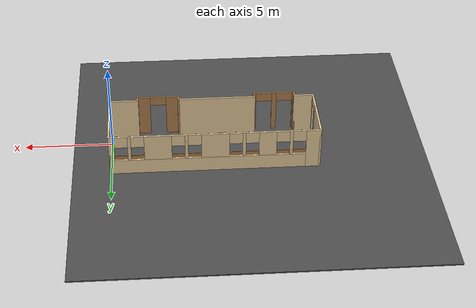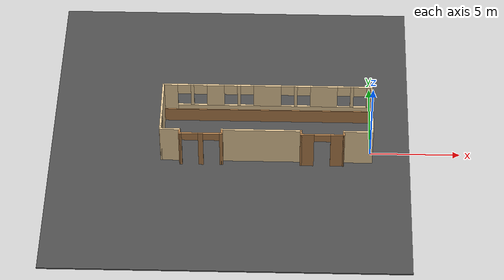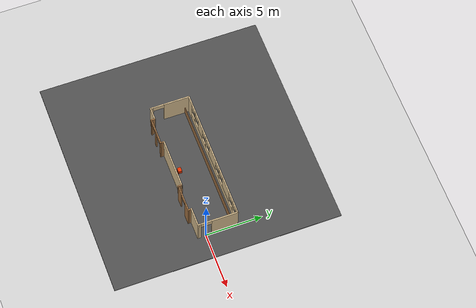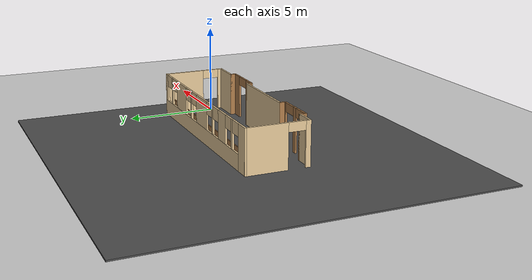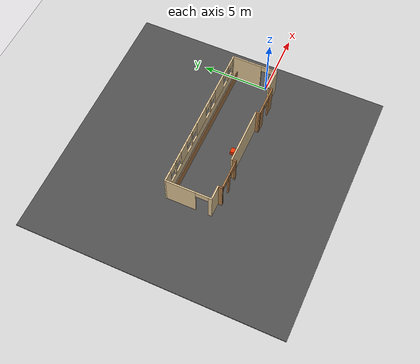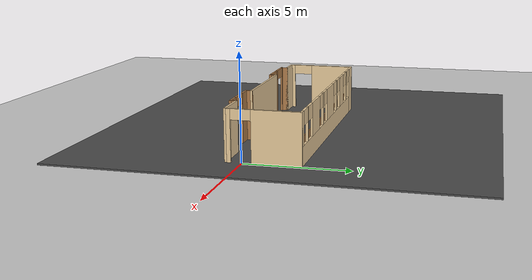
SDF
<sdf version="1.6">
 <world name="default">
  <light name="sun" type="directional">
   <pose>0 0 10 0 -0 0</pose>
   <diffuse>0.8 0.8 0.8 1</diffuse>
   <specular>0.1 0.1 0.1 1</specular>
   <attenuation>
    <range>1000</range>
    <constant>0.9</constant>
    <linear>0.01</linear>
    <quadratic>0.001</quadratic>
   </attenuation>
   <direction>-0.5 0.5 -1</direction>
  </light>
  <model name="ground_plane">
   <static>1</static>
   <link name="link">
    <collision name="collision">
     <geometry><plane><normal>0 0 1</normal><size>100 100</size></plane></geometry>
     <surface><friction><ode><mu>100</mu><mu2>50</mu2></ode></friction></surface>
    </collision>
    <visual name="visual">
     <cast_shadows>0</cast_shadows>
     <geometry><plane><normal>0 0 1</normal><size>100 100</size></plane></geometry>
     <material>
      <script><uri>file://media/materials/scripts/gazebo.material</uri><name>Gazebo/Grey</name></script>
     </material>
    </visual>
   </link>
  </model>
  <physics name="default_physics" default="0" type="ode">
   <max_step_size>0.01</max_step_size>
   <real_time_factor>1</real_time_factor>
   <real_time_update_rate>100</real_time_update_rate>
  </physics>
  <gravity>0 0 -9.8</gravity>
  <magnetic_field>6e-06 2.3e-05 -4.2e-05</magnetic_field>
  <atmosphere type="adiabatic"/>
  <scene><ambient>0.4 0.4 0.4 1</ambient><background>0.7 0.7 0.7 1</background><shadows>1</shadows></scene>
  <spherical_coordinates>
   <surface_model>EARTH_WGS84</surface_model>
   <latitude_deg>0</latitude_deg>
   <longitude_deg>0</longitude_deg>
   <elevation>0</elevation>
   <heading_deg>0</heading_deg>
  </spherical_coordinates>
  <model name="LawHall_Floor4.sdf">
   <link name="Wall_0">
    <pose>0 1.8775 0 0 -0 0</pose>
    <visual name="Wall_0_Visual_4">
     <pose>-1.606 0 1.72 0 -0 0</pose>
     <geometry><box><size>0.178 0.1 1.56</size></box></geometry>
     <material>
      <script><uri>file://media/materials/scripts/gazebo.material</uri><name>Gazebo/Grey</name></script>
      <ambient>0.921569 0.807843 0.615686 1</ambient>
      <diffuse>0.7 0.7 0.7 1</diffuse>
      <specular>0.01 0.01 0.01 1</specular>
      <emissive>0 0 0 1</emissive>
     </material>
    </visual>
    <visual name="Wall_0_Visual_15">
     <pose>2.034 0 2.158 0 -0 0</pose>
     <geometry><box><size>0.73 0.1 0.684</size></box></geometry>
     <material>
      <script><uri>file://media/materials/scripts/gazebo.material</uri><name>Gazebo/Grey</name></script>
      <ambient>0.921569 0.807843 0.615686 1</ambient>
      <diffuse>0.7 0.7 0.7 1</diffuse>
      <specular>0.01 0.01 0.01 1</specular>
      <emissive>0 0 0 1</emissive>
     </material>
    </visual>
    <visual name="Wall_0_Visual_0">
     <pose>-5.4555 0 1.25 0 -0 0</pose>
     <geometry><box><size>0.841 0.1 2.5</size></box></geometry>
     <material>
      <script><uri>file://media/materials/scripts/gazebo.material</uri><name>Gazebo/Grey</name></script>
      <ambient>0.921569 0.807843 0.615686 1</ambient>
      <diffuse>0.7 0.7 0.7 1</diffuse>
      <specular>0.01 0.01 0.01 1</specular>
      <emissive>0 0 0 1</emissive>
     </material>
    </visual>
    <visual name="Wall_0_Visual_7">
     <pose>3.154 0 1.72 0 -0 0</pose>
     <geometry><box><size>1.51 0.1 1.56</size></box></geometry>
     <material>
      <script><uri>file://media/materials/scripts/gazebo.material</uri><name>Gazebo/Grey</name></script>
      <ambient>0.921569 0.807843 0.615686 1</ambient>
      <diffuse>0.7 0.7 0.7 1</diffuse>
      <specular>0.01 0.01 0.01 1</specular>
      <emissive>0 0 0 1</emissive>
     </material>
    </visual>
    <visual name="Wall_0_Visual_17">
     <pose>5.184 0 2.158 0 -0 0</pose>
     <geometry><box><size>0.73 0.1 0.684</size></box></geometry>
     <material>
      <script><uri>file://media/materials/scripts/gazebo.material</uri><name>Gazebo/Grey</name></script>
      <ambient>0.921569 0.807843 0.615686 1</ambient>
      <diffuse>0.7 0.7 0.7 1</diffuse>
      <specular>0.01 0.01 0.01 1</specular>
      <emissive>0 0 0 1</emissive>
     </material>
    </visual>
    <visual name="Wall_0_Visual_6">
     <pose>1.5805 0 1.72 0 -0 0</pose>
     <geometry><box><size>0.177 0.1 1.56</size></box></geometry>
     <material>
      <script><uri>file://media/materials/scripts/gazebo.material</uri><name>Gazebo/Grey</name></script>
      <ambient>0.921569 0.807843 0.615686 1</ambient>
      <diffuse>0.7 0.7 0.7 1</diffuse>
      <specular>0.01 0.01 0.01 1</specular>
      <emissive>0 0 0 1</emissive>
     </material>
    </visual>
    <visual name="Wall_0_Visual_2">
     <pose>-4.216 0 1.72 0 -0 0</pose>
     <geometry><box><size>0.178 0.1 1.56</size></box></geometry>
     <material>
      <script><uri>file://media/materials/scripts/gazebo.material</uri><name>Gazebo/Grey</name></script>
      <ambient>0.921569 0.807843 0.615686 1</ambient>
      <diffuse>0.7 0.7 0.7 1</diffuse>
      <specular>0.01 0.01 0.01 1</specular>
      <emissive>0 0 0 1</emissive>
     </material>
    </visual>
    <visual name="Wall_0_Visual_9">
     <pose>5.7125 0 1.72 0 -0 0</pose>
     <geometry><box><size>0.327 0.1 1.56</size></box></geometry>
     <material>
      <script><uri>file://media/materials/scripts/gazebo.material</uri><name>Gazebo/Grey</name></script>
      <ambient>0.921569 0.807843 0.615686 1</ambient>
      <diffuse>0.7 0.7 0.7 1</diffuse>
      <specular>0.01 0.01 0.01 1</specular>
      <emissive>0 0 0 1</emissive>
     </material>
    </visual>
    <visual name="Wall_0_Visual_16">
     <pose>4.274 0 2.158 0 -0 0</pose>
     <geometry><box><size>0.73 0.1 0.684</size></box></geometry>
     <material>
      <script><uri>file://media/materials/scripts/gazebo.material</uri><name>Gazebo/Grey</name></script>
      <ambient>0.921569 0.807843 0.615686 1</ambient>
      <diffuse>0.7 0.7 0.7 1</diffuse>
      <specular>0.01 0.01 0.01 1</specular>
      <emissive>0 0 0 1</emissive>
     </material>
    </visual>
    <visual name="Wall_0_Visual_10">
     <pose>-4.67 0 2.158 0 -0 0</pose>
     <geometry><box><size>0.73 0.1 0.684</size></box></geometry>
     <material>
      <script><uri>file://media/materials/scripts/gazebo.material</uri><name>Gazebo/Grey</name></script>
      <ambient>0.921569 0.807843 0.615686 1</ambient>
      <diffuse>0.7 0.7 0.7 1</diffuse>
      <specular>0.01 0.01 0.01 1</specular>
      <emissive>0 0 0 1</emissive>
     </material>
    </visual>
    <visual name="Wall_0_Visual_11">
     <pose>-3.762 0 2.158 0 -0 0</pose>
     <geometry><box><size>0.73 0.1 0.684</size></box></geometry>
     <material>
      <script><uri>file://media/materials/scripts/gazebo.material</uri><name>Gazebo/Grey</name></script>
      <ambient>0.921569 0.807843 0.615686 1</ambient>
      <diffuse>0.7 0.7 0.7 1</diffuse>
      <specular>0.01 0.01 0.01 1</specular>
      <emissive>0 0 0 1</emissive>
     </material>
    </visual>
    <visual name="Wall_0_Visual_5">
     <pose>-0.0125 0 1.72 0 -0 0</pose>
     <geometry><box><size>1.549 0.1 1.56</size></box></geometry>
     <material>
      <script><uri>file://media/materials/scripts/gazebo.material</uri><name>Gazebo/Grey</name></script>
      <ambient>0.921569 0.807843 0.615686 1</ambient>
      <diffuse>0.7 0.7 0.7 1</diffuse>
      <specular>0.01 0.01 0.01 1</specular>
      <emissive>0 0 0 1</emissive>
     </material>
    </visual>
    <visual name="Wall_0_Visual_14">
     <pose>1.127 0 2.158 0 -0 0</pose>
     <geometry><box><size>0.73 0.1 0.684</size></box></geometry>
     <material>
      <script><uri>file://media/materials/scripts/gazebo.material</uri><name>Gazebo/Grey</name></script>
      <ambient>0.921569 0.807843 0.615686 1</ambient>
      <diffuse>0.7 0.7 0.7 1</diffuse>
      <specular>0.01 0.01 0.01 1</specular>
      <emissive>0 0 0 1</emissive>
     </material>
    </visual>
    <visual name="Wall_0_Visual_13">
     <pose>-1.152 0 2.158 0 -0 0</pose>
     <geometry><box><size>0.73 0.1 0.684</size></box></geometry>
     <material>
      <script><uri>file://media/materials/scripts/gazebo.material</uri><name>Gazebo/Grey</name></script>
      <ambient>0.921569 0.807843 0.615686 1</ambient>
      <diffuse>0.7 0.7 0.7 1</diffuse>
      <specular>0.01 0.01 0.01 1</specular>
      <emissive>0 0 0 1</emissive>
     </material>
    </visual>
    <visual name="Wall_0_Visual_12">
     <pose>-2.06 0 2.158 0 -0 0</pose>
     <geometry><box><size>0.73 0.1 0.684</size></box></geometry>
     <material>
      <script><uri>file://media/materials/scripts/gazebo.material</uri><name>Gazebo/Grey</name></script>
      <ambient>0.921569 0.807843 0.615686 1</ambient>
      <diffuse>0.7 0.7 0.7 1</diffuse>
      <specular>0.01 0.01 0.01 1</specular>
      <emissive>0 0 0 1</emissive>
     </material>
    </visual>
    <visual name="Wall_0_Visual_8">
     <pose>4.729 0 1.72 0 -0 0</pose>
     <geometry><box><size>0.18 0.1 1.56</size></box></geometry>
     <material>
      <script><uri>file://media/materials/scripts/gazebo.material</uri><name>Gazebo/Grey</name></script>
      <ambient>0.921569 0.807843 0.615686 1</ambient>
      <diffuse>0.7 0.7 0.7 1</diffuse>
      <specular>0.01 0.01 0.01 1</specular>
      <emissive>0 0 0 1</emissive>
     </material>
    </visual>
    <visual name="Wall_0_Visual_3">
     <pose>-2.911 0 1.72 0 -0 0</pose>
     <geometry><box><size>0.972 0.1 1.56</size></box></geometry>
     <material>
      <script><uri>file://media/materials/scripts/gazebo.material</uri><name>Gazebo/Grey</name></script>
      <ambient>0.921569 0.807843 0.615686 1</ambient>
      <diffuse>0.7 0.7 0.7 1</diffuse>
      <specular>0.01 0.01 0.01 1</specular>
      <emissive>0 0 0 1</emissive>
     </material>
    </visual>
    <visual name="Wall_0_Visual_1">
     <pose>0.4205 0 0.47 0 -0 0</pose>
     <geometry><box><size>10.911 0.1 0.94</size></box></geometry>
     <material>
      <script><uri>file://media/materials/scripts/gazebo.material</uri><name>Gazebo/Grey</name></script>
      <ambient>0.921569 0.807843 0.615686 1</ambient>
      <diffuse>0.7 0.7 0.7 1</diffuse>
      <specular>0.01 0.01 0.01 1</specular>
      <emissive>0 0 0 1</emissive>
     </material>
    </visual>
    <collision name="Wall_0_Collision_11">
     <pose>-3.762 0 2.158 0 -0 0</pose>
     <geometry><box><size>0.73 0.1 0.684</size></box></geometry>
     <surface>
      <friction>
       <ode><mu>1</mu><mu2>1</mu2><fdir1>0 0 0</fdir1><slip1>0</slip1><slip2>0</slip2></ode>
       <torsional>
        <coefficient>1</coefficient>
        <patch_radius>0</patch_radius>
        <surface_radius>0</surface_radius>
        <use_patch_radius>1</use_patch_radius>
        <ode><slip>0</slip></ode>
       </torsional>
      </friction>
      <bounce><restitution_coefficient>0</restitution_coefficient><threshold>1e+06</threshold></bounce>
      <contact>
       <collide_without_contact>0</collide_without_contact>
       <collide_without_contact_bitmask>1</collide_without_contact_bitmask>
       <collide_bitmask>1</collide_bitmask>
       <ode>
        <soft_cfm>0</soft_cfm>
        <soft_erp>0.2</soft_erp>
        <kp>1e+13</kp>
        <kd>1</kd>
        <max_vel>0.01</max_vel>
        <min_depth>0</min_depth>
       </ode>
       <bullet>
        <split_impulse>1</split_impulse>
        <split_impulse_penetration_threshold>-0.01</split_impulse_penetration_threshold>
        <soft_cfm>0</soft_cfm>
        <soft_erp>0.2</soft_erp>
        <kp>1e+13</kp>
        <kd>1</kd>
       </bullet>
      </contact>
     </surface>
    </collision>
    <collision name="Wall_0_Collision_7">
     <pose>3.154 0 1.72 0 -0 0</pose>
     <geometry><box><size>1.51 0.1 1.56</size></box></geometry>
     <surface>
      <friction>
       <ode><mu>1</mu><mu2>1</mu2><fdir1>0 0 0</fdir1><slip1>0</slip1><slip2>0</slip2></ode>
       <torsional>
        <coefficient>1</coefficient>
        <patch_radius>0</patch_radius>
        <surface_radius>0</surface_radius>
        <use_patch_radius>1</use_patch_radius>
        <ode><slip>0</slip></ode>
       </torsional>
      </friction>
      <bounce><restitution_coefficient>0</restitution_coefficient><threshold>1e+06</threshold></bounce>
      <contact>
       <collide_without_contact>0</collide_without_contact>
       <collide_without_contact_bitmask>1</collide_without_contact_bitmask>
       <collide_bitmask>1</collide_bitmask>
       <ode>
        <soft_cfm>0</soft_cfm>
        <soft_erp>0.2</soft_erp>
        <kp>1e+13</kp>
        <kd>1</kd>
        <max_vel>0.01</max_vel>
        <min_depth>0</min_depth>
       </ode>
       <bullet>
        <split_impulse>1</split_impulse>
        <split_impulse_penetration_threshold>-0.01</split_impulse_penetration_threshold>
        <soft_cfm>0</soft_cfm>
        <soft_erp>0.2</soft_erp>
        <kp>1e+13</kp>
        <kd>1</kd>
       </bullet>
      </contact>
     </surface>
    </collision>
    <collision name="Wall_0_Collision_14">
     <pose>1.127 0 2.158 0 -0 0</pose>
     <geometry><box><size>0.73 0.1 0.684</size></box></geometry>
     <surface>
      <friction>
       <ode><mu>1</mu><mu2>1</mu2><fdir1>0 0 0</fdir1><slip1>0</slip1><slip2>0</slip2></ode>
       <torsional>
        <coefficient>1</coefficient>
        <patch_radius>0</patch_radius>
        <surface_radius>0</surface_radius>
        <use_patch_radius>1</use_patch_radius>
        <ode><slip>0</slip></ode>
       </torsional>
      </friction>
      <bounce><restitution_coefficient>0</restitution_coefficient><threshold>1e+06</threshold></bounce>
      <contact>
       <collide_without_contact>0</collide_without_contact>
       <collide_without_contact_bitmask>1</collide_without_contact_bitmask>
       <collide_bitmask>1</collide_bitmask>
       <ode>
        <soft_cfm>0</soft_cfm>
        <soft_erp>0.2</soft_erp>
        <kp>1e+13</kp>
        <kd>1</kd>
        <max_vel>0.01</max_vel>
        <min_depth>0</min_depth>
       </ode>
       <bullet>
        <split_impulse>1</split_impulse>
        <split_impulse_penetration_threshold>-0.01</split_impulse_penetration_threshold>
        <soft_cfm>0</soft_cfm>
        <soft_erp>0.2</soft_erp>
        <kp>1e+13</kp>
        <kd>1</kd>
       </bullet>
      </contact>
     </surface>
    </collision>
    <collision name="Wall_0_Collision_5">
     <pose>-0.0125 0 1.72 0 -0 0</pose>
     <geometry><box><size>1.549 0.1 1.56</size></box></geometry>
     <surface>
      <friction>
       <ode><mu>1</mu><mu2>1</mu2><fdir1>0 0 0</fdir1><slip1>0</slip1><slip2>0</slip2></ode>
       <torsional>
        <coefficient>1</coefficient>
        <patch_radius>0</patch_radius>
        <surface_radius>0</surface_radius>
        <use_patch_radius>1</use_patch_radius>
        <ode><slip>0</slip></ode>
       </torsional>
      </friction>
      <bounce><restitution_coefficient>0</restitution_coefficient><threshold>1e+06</threshold></bounce>
      <contact>
       <collide_without_contact>0</collide_without_contact>
       <collide_without_contact_bitmask>1</collide_without_contact_bitmask>
       <collide_bitmask>1</collide_bitmask>
       <ode>
        <soft_cfm>0</soft_cfm>
        <soft_erp>0.2</soft_erp>
        <kp>1e+13</kp>
        <kd>1</kd>
        <max_vel>0.01</max_vel>
        <min_depth>0</min_depth>
       </ode>
       <bullet>
        <split_impulse>1</split_impulse>
        <split_impulse_penetration_threshold>-0.01</split_impulse_penetration_threshold>
        <soft_cfm>0</soft_cfm>
        <soft_erp>0.2</soft_erp>
        <kp>1e+13</kp>
        <kd>1</kd>
       </bullet>
      </contact>
     </surface>
    </collision>
    <collision name="Wall_0_Collision_9">
     <pose>5.7125 0 1.72 0 -0 0</pose>
     <geometry><box><size>0.327 0.1 1.56</size></box></geometry>
     <surface>
      <friction>
       <ode><mu>1</mu><mu2>1</mu2><fdir1>0 0 0</fdir1><slip1>0</slip1><slip2>0</slip2></ode>
       <torsional>
        <coefficient>1</coefficient>
        <patch_radius>0</patch_radius>
        <surface_radius>0</surface_radius>
        <use_patch_radius>1</use_patch_radius>
        <ode><slip>0</slip></ode>
       </torsional>
      </friction>
      <bounce><restitution_coefficient>0</restitution_coefficient><threshold>1e+06</threshold></bounce>
      <contact>
       <collide_without_contact>0</collide_without_contact>
       <collide_without_contact_bitmask>1</collide_without_contact_bitmask>
       <collide_bitmask>1</collide_bitmask>
       <ode>
        <soft_cfm>0</soft_cfm>
        <soft_erp>0.2</soft_erp>
        <kp>1e+13</kp>
        <kd>1</kd>
        <max_vel>0.01</max_vel>
        <min_depth>0</min_depth>
       </ode>
       <bullet>
        <split_impulse>1</split_impulse>
        <split_impulse_penetration_threshold>-0.01</split_impulse_penetration_threshold>
        <soft_cfm>0</soft_cfm>
        <soft_erp>0.2</soft_erp>
        <kp>1e+13</kp>
        <kd>1</kd>
       </bullet>
      </contact>
     </surface>
    </collision>
    <collision name="Wall_0_Collision_2">
     <pose>-4.216 0 1.72 0 -0 0</pose>
     <geometry><box><size>0.178 0.1 1.56</size></box></geometry>
     <surface>
      <friction>
       <ode><mu>1</mu><mu2>1</mu2><fdir1>0 0 0</fdir1><slip1>0</slip1><slip2>0</slip2></ode>
       <torsional>
        <coefficient>1</coefficient>
        <patch_radius>0</patch_radius>
        <surface_radius>0</surface_radius>
        <use_patch_radius>1</use_patch_radius>
        <ode><slip>0</slip></ode>
       </torsional>
      </friction>
      <bounce><restitution_coefficient>0</restitution_coefficient><threshold>1e+06</threshold></bounce>
      <contact>
       <collide_without_contact>0</collide_without_contact>
       <collide_without_contact_bitmask>1</collide_without_contact_bitmask>
       <collide_bitmask>1</collide_bitmask>
       <ode>
        <soft_cfm>0</soft_cfm>
        <soft_erp>0.2</soft_erp>
        <kp>1e+13</kp>
        <kd>1</kd>
        <max_vel>0.01</max_vel>
        <min_depth>0</min_depth>
       </ode>
       <bullet>
        <split_impulse>1</split_impulse>
        <split_impulse_penetration_threshold>-0.01</split_impulse_penetration_threshold>
        <soft_cfm>0</soft_cfm>
        <soft_erp>0.2</soft_erp>
        <kp>1e+13</kp>
        <kd>1</kd>
       </bullet>
      </contact>
     </surface>
    </collision>
    <collision name="Wall_0_Collision_3">
     <pose>-2.911 0 1.72 0 -0 0</pose>
     <geometry><box><size>0.972 0.1 1.56</size></box></geometry>
     <surface>
      <friction>
       <ode><mu>1</mu><mu2>1</mu2><fdir1>0 0 0</fdir1><slip1>0</slip1><slip2>0</slip2></ode>
       <torsional>
        <coefficient>1</coefficient>
        <patch_radius>0</patch_radius>
        <surface_radius>0</surface_radius>
        <use_patch_radius>1</use_patch_radius>
        <ode><slip>0</slip></ode>
       </torsional>
      </friction>
      <bounce><restitution_coefficient>0</restitution_coefficient><threshold>1e+06</threshold></bounce>
      <contact>
       <collide_without_contact>0</collide_without_contact>
       <collide_without_contact_bitmask>1</collide_without_contact_bitmask>
       <collide_bitmask>1</collide_bitmask>
       <ode>
        <soft_cfm>0</soft_cfm>
        <soft_erp>0.2</soft_erp>
        <kp>1e+13</kp>
        <kd>1</kd>
        <max_vel>0.01</max_vel>
        <min_depth>0</min_depth>
       </ode>
       <bullet>
        <split_impulse>1</split_impulse>
        <split_impulse_penetration_threshold>-0.01</split_impulse_penetration_threshold>
        <soft_cfm>0</soft_cfm>
        <soft_erp>0.2</soft_erp>
        <kp>1e+13</kp>
        <kd>1</kd>
       </bullet>
      </contact>
     </surface>
    </collision>
    <collision name="Wall_0_Collision_6">
     <pose>1.5805 0 1.72 0 -0 0</pose>
     <geometry><box><size>0.177 0.1 1.56</size></box></geometry>
     <surface>
      <friction>
       <ode><mu>1</mu><mu2>1</mu2><fdir1>0 0 0</fdir1><slip1>0</slip1><slip2>0</slip2></ode>
       <torsional>
        <coefficient>1</coefficient>
        <patch_radius>0</patch_radius>
        <surface_radius>0</surface_radius>
        <use_patch_radius>1</use_patch_radius>
        <ode><slip>0</slip></ode>
       </torsional>
      </friction>
      <bounce><restitution_coefficient>0</restitution_coefficient><threshold>1e+06</threshold></bounce>
      <contact>
       <collide_without_contact>0</collide_without_contact>
       <collide_without_contact_bitmask>1</collide_without_contact_bitmask>
       <collide_bitmask>1</collide_bitmask>
       <ode>
        <soft_cfm>0</soft_cfm>
        <soft_erp>0.2</soft_erp>
        <kp>1e+13</kp>
        <kd>1</kd>
        <max_vel>0.01</max_vel>
        <min_depth>0</min_depth>
       </ode>
       <bullet>
        <split_impulse>1</split_impulse>
        <split_impulse_penetration_threshold>-0.01</split_impulse_penetration_threshold>
        <soft_cfm>0</soft_cfm>
        <soft_erp>0.2</soft_erp>
        <kp>1e+13</kp>
        <kd>1</kd>
       </bullet>
      </contact>
     </surface>
    </collision>
    <collision name="Wall_0_Collision_13">
     <pose>-1.152 0 2.158 0 -0 0</pose>
     <geometry><box><size>0.73 0.1 0.684</size></box></geometry>
     <surface>
      <friction>
       <ode><mu>1</mu><mu2>1</mu2><fdir1>0 0 0</fdir1><slip1>0</slip1><slip2>0</slip2></ode>
       <torsional>
        <coefficient>1</coefficient>
        <patch_radius>0</patch_radius>
        <surface_radius>0</surface_radius>
        <use_patch_radius>1</use_patch_radius>
        <ode><slip>0</slip></ode>
       </torsional>
      </friction>
      <bounce><restitution_coefficient>0</restitution_coefficient><threshold>1e+06</threshold></bounce>
      <contact>
       <collide_without_contact>0</collide_without_contact>
       <collide_without_contact_bitmask>1</collide_without_contact_bitmask>
       <collide_bitmask>1</collide_bitmask>
       <ode>
        <soft_cfm>0</soft_cfm>
        <soft_erp>0.2</soft_erp>
        <kp>1e+13</kp>
        <kd>1</kd>
        <max_vel>0.01</max_vel>
        <min_depth>0</min_depth>
       </ode>
       <bullet>
        <split_impulse>1</split_impulse>
        <split_impulse_penetration_threshold>-0.01</split_impulse_penetration_threshold>
        <soft_cfm>0</soft_cfm>
        <soft_erp>0.2</soft_erp>
        <kp>1e+13</kp>
        <kd>1</kd>
       </bullet>
      </contact>
     </surface>
    </collision>
    <collision name="Wall_0_Collision_15">
     <pose>2.034 0 2.158 0 -0 0</pose>
     <geometry><box><size>0.73 0.1 0.684</size></box></geometry>
     <surface>
      <friction>
       <ode><mu>1</mu><mu2>1</mu2><fdir1>0 0 0</fdir1><slip1>0</slip1><slip2>0</slip2></ode>
       <torsional>
        <coefficient>1</coefficient>
        <patch_radius>0</patch_radius>
        <surface_radius>0</surface_radius>
        <use_patch_radius>1</use_patch_radius>
        <ode><slip>0</slip></ode>
       </torsional>
      </friction>
      <bounce><restitution_coefficient>0</restitution_coefficient><threshold>1e+06</threshold></bounce>
      <contact>
       <collide_without_contact>0</collide_without_contact>
       <collide_without_contact_bitmask>1</collide_without_contact_bitmask>
       <collide_bitmask>1</collide_bitmask>
       <ode>
        <soft_cfm>0</soft_cfm>
        <soft_erp>0.2</soft_erp>
        <kp>1e+13</kp>
        <kd>1</kd>
        <max_vel>0.01</max_vel>
        <min_depth>0</min_depth>
       </ode>
       <bullet>
        <split_impulse>1</split_impulse>
        <split_impulse_penetration_threshold>-0.01</split_impulse_penetration_threshold>
        <soft_cfm>0</soft_cfm>
        <soft_erp>0.2</soft_erp>
        <kp>1e+13</kp>
        <kd>1</kd>
       </bullet>
      </contact>
     </surface>
    </collision>
    <collision name="Wall_0_Collision_1">
     <pose>0.4205 0 0.47 0 -0 0</pose>
     <geometry><box><size>10.911 0.1 0.94</size></box></geometry>
     <surface>
      <friction>
       <ode><mu>1</mu><mu2>1</mu2><fdir1>0 0 0</fdir1><slip1>0</slip1><slip2>0</slip2></ode>
       <torsional>
        <coefficient>1</coefficient>
        <patch_radius>0</patch_radius>
        <surface_radius>0</surface_radius>
        <use_patch_radius>1</use_patch_radius>
        <ode><slip>0</slip></ode>
       </torsional>
      </friction>
      <bounce><restitution_coefficient>0</restitution_coefficient><threshold>1e+06</threshold></bounce>
      <contact>
       <collide_without_contact>0</collide_without_contact>
       <collide_without_contact_bitmask>1</collide_without_contact_bitmask>
       <collide_bitmask>1</collide_bitmask>
       <ode>
        <soft_cfm>0</soft_cfm>
        <soft_erp>0.2</soft_erp>
        <kp>1e+13</kp>
        <kd>1</kd>
        <max_vel>0.01</max_vel>
        <min_depth>0</min_depth>
       </ode>
       <bullet>
        <split_impulse>1</split_impulse>
        <split_impulse_penetration_threshold>-0.01</split_impulse_penetration_threshold>
        <soft_cfm>0</soft_cfm>
        <soft_erp>0.2</soft_erp>
        <kp>1e+13</kp>
        <kd>1</kd>
       </bullet>
      </contact>
     </surface>
    </collision>
    <collision name="Wall_0_Collision_16">
     <pose>4.274 0 2.158 0 -0 0</pose>
     <geometry><box><size>0.73 0.1 0.684</size></box></geometry>
     <surface>
      <friction>
       <ode><mu>1</mu><mu2>1</mu2><fdir1>0 0 0</fdir1><slip1>0</slip1><slip2>0</slip2></ode>
       <torsional>
        <coefficient>1</coefficient>
        <patch_radius>0</patch_radius>
        <surface_radius>0</surface_radius>
        <use_patch_radius>1</use_patch_radius>
        <ode><slip>0</slip></ode>
       </torsional>
      </friction>
      <bounce><restitution_coefficient>0</restitution_coefficient><threshold>1e+06</threshold></bounce>
      <contact>
       <collide_without_contact>0</collide_without_contact>
       <collide_without_contact_bitmask>1</collide_without_contact_bitmask>
       <collide_bitmask>1</collide_bitmask>
       <ode>
        <soft_cfm>0</soft_cfm>
        <soft_erp>0.2</soft_erp>
        <kp>1e+13</kp>
        <kd>1</kd>
        <max_vel>0.01</max_vel>
        <min_depth>0</min_depth>
       </ode>
       <bullet>
        <split_impulse>1</split_impulse>
        <split_impulse_penetration_threshold>-0.01</split_impulse_penetration_threshold>
        <soft_cfm>0</soft_cfm>
        <soft_erp>0.2</soft_erp>
        <kp>1e+13</kp>
        <kd>1</kd>
       </bullet>
      </contact>
     </surface>
    </collision>
    <collision name="Wall_0_Collision_12">
     <pose>-2.06 0 2.158 0 -0 0</pose>
     <geometry><box><size>0.73 0.1 0.684</size></box></geometry>
     <surface>
      <friction>
       <ode><mu>1</mu><mu2>1</mu2><fdir1>0 0 0</fdir1><slip1>0</slip1><slip2>0</slip2></ode>
       <torsional>
        <coefficient>1</coefficient>
        <patch_radius>0</patch_radius>
        <surface_radius>0</surface_radius>
        <use_patch_radius>1</use_patch_radius>
        <ode><slip>0</slip></ode>
       </torsional>
      </friction>
      <bounce><restitution_coefficient>0</restitution_coefficient><threshold>1e+06</threshold></bounce>
      <contact>
       <collide_without_contact>0</collide_without_contact>
       <collide_without_contact_bitmask>1</collide_without_contact_bitmask>
       <collide_bitmask>1</collide_bitmask>
       <ode>
        <soft_cfm>0</soft_cfm>
        <soft_erp>0.2</soft_erp>
        <kp>1e+13</kp>
        <kd>1</kd>
        <max_vel>0.01</max_vel>
        <min_depth>0</min_depth>
       </ode>
       <bullet>
        <split_impulse>1</split_impulse>
        <split_impulse_penetration_threshold>-0.01</split_impulse_penetration_threshold>
        <soft_cfm>0</soft_cfm>
        <soft_erp>0.2</soft_erp>
        <kp>1e+13</kp>
        <kd>1</kd>
       </bullet>
      </contact>
     </surface>
    </collision>
    <collision name="Wall_0_Collision_4">
     <pose>-1.606 0 1.72 0 -0 0</pose>
     <geometry><box><size>0.178 0.1 1.56</size></box></geometry>
     <surface>
      <friction>
       <ode><mu>1</mu><mu2>1</mu2><fdir1>0 0 0</fdir1><slip1>0</slip1><slip2>0</slip2></ode>
       <torsional>
        <coefficient>1</coefficient>
        <patch_radius>0</patch_radius>
        <surface_radius>0</surface_radius>
        <use_patch_radius>1</use_patch_radius>
        <ode><slip>0</slip></ode>
       </torsional>
      </friction>
      <bounce><restitution_coefficient>0</restitution_coefficient><threshold>1e+06</threshold></bounce>
      <contact>
       <collide_without_contact>0</collide_without_contact>
       <collide_without_contact_bitmask>1</collide_without_contact_bitmask>
       <collide_bitmask>1</collide_bitmask>
       <ode>
        <soft_cfm>0</soft_cfm>
        <soft_erp>0.2</soft_erp>
        <kp>1e+13</kp>
        <kd>1</kd>
        <max_vel>0.01</max_vel>
        <min_depth>0</min_depth>
       </ode>
       <bullet>
        <split_impulse>1</split_impulse>
        <split_impulse_penetration_threshold>-0.01</split_impulse_penetration_threshold>
        <soft_cfm>0</soft_cfm>
        <soft_erp>0.2</soft_erp>
        <kp>1e+13</kp>
        <kd>1</kd>
       </bullet>
      </contact>
     </surface>
    </collision>
    <collision name="Wall_0_Collision_17">
     <pose>5.184 0 2.158 0 -0 0</pose>
     <geometry><box><size>0.73 0.1 0.684</size></box></geometry>
     <surface>
      <friction>
       <ode><mu>1</mu><mu2>1</mu2><fdir1>0 0 0</fdir1><slip1>0</slip1><slip2>0</slip2></ode>
       <torsional>
        <coefficient>1</coefficient>
        <patch_radius>0</patch_radius>
        <surface_radius>0</surface_radius>
        <use_patch_radius>1</use_patch_radius>
        <ode><slip>0</slip></ode>
       </torsional>
      </friction>
      <bounce><restitution_coefficient>0</restitution_coefficient><threshold>1e+06</threshold></bounce>
      <contact>
       <collide_without_contact>0</collide_without_contact>
       <collide_without_contact_bitmask>1</collide_without_contact_bitmask>
       <collide_bitmask>1</collide_bitmask>
       <ode>
        <soft_cfm>0</soft_cfm>
        <soft_erp>0.2</soft_erp>
        <kp>1e+13</kp>
        <kd>1</kd>
        <max_vel>0.01</max_vel>
        <min_depth>0</min_depth>
       </ode>
       <bullet>
        <split_impulse>1</split_impulse>
        <split_impulse_penetration_threshold>-0.01</split_impulse_penetration_threshold>
        <soft_cfm>0</soft_cfm>
        <soft_erp>0.2</soft_erp>
        <kp>1e+13</kp>
        <kd>1</kd>
       </bullet>
      </contact>
     </surface>
    </collision>
    <collision name="Wall_0_Collision_8">
     <pose>4.729 0 1.72 0 -0 0</pose>
     <geometry><box><size>0.18 0.1 1.56</size></box></geometry>
     <surface>
      <friction>
       <ode><mu>1</mu><mu2>1</mu2><fdir1>0 0 0</fdir1><slip1>0</slip1><slip2>0</slip2></ode>
       <torsional>
        <coefficient>1</coefficient>
        <patch_radius>0</patch_radius>
        <surface_radius>0</surface_radius>
        <use_patch_radius>1</use_patch_radius>
        <ode><slip>0</slip></ode>
       </torsional>
      </friction>
      <bounce><restitution_coefficient>0</restitution_coefficient><threshold>1e+06</threshold></bounce>
      <contact>
       <collide_without_contact>0</collide_without_contact>
       <collide_without_contact_bitmask>1</collide_without_contact_bitmask>
       <collide_bitmask>1</collide_bitmask>
       <ode>
        <soft_cfm>0</soft_cfm>
        <soft_erp>0.2</soft_erp>
        <kp>1e+13</kp>
        <kd>1</kd>
        <max_vel>0.01</max_vel>
        <min_depth>0</min_depth>
       </ode>
       <bullet>
        <split_impulse>1</split_impulse>
        <split_impulse_penetration_threshold>-0.01</split_impulse_penetration_threshold>
        <soft_cfm>0</soft_cfm>
        <soft_erp>0.2</soft_erp>
        <kp>1e+13</kp>
        <kd>1</kd>
       </bullet>
      </contact>
     </surface>
    </collision>
    <collision name="Wall_0_Collision_0">
     <pose>-5.4555 0 1.25 0 -0 0</pose>
     <geometry><box><size>0.841 0.1 2.5</size></box></geometry>
     <surface>
      <friction>
       <ode><mu>1</mu><mu2>1</mu2><fdir1>0 0 0</fdir1><slip1>0</slip1><slip2>0</slip2></ode>
       <torsional>
        <coefficient>1</coefficient>
        <patch_radius>0</patch_radius>
        <surface_radius>0</surface_radius>
        <use_patch_radius>1</use_patch_radius>
        <ode><slip>0</slip></ode>
       </torsional>
      </friction>
      <bounce><restitution_coefficient>0</restitution_coefficient><threshold>1e+06</threshold></bounce>
      <contact>
       <collide_without_contact>0</collide_without_contact>
       <collide_without_contact_bitmask>1</collide_without_contact_bitmask>
       <collide_bitmask>1</collide_bitmask>
       <ode>
        <soft_cfm>0</soft_cfm>
        <soft_erp>0.2</soft_erp>
        <kp>1e+13</kp>
        <kd>1</kd>
        <max_vel>0.01</max_vel>
        <min_depth>0</min_depth>
       </ode>
       <bullet>
        <split_impulse>1</split_impulse>
        <split_impulse_penetration_threshold>-0.01</split_impulse_penetration_threshold>
        <soft_cfm>0</soft_cfm>
        <soft_erp>0.2</soft_erp>
        <kp>1e+13</kp>
        <kd>1</kd>
       </bullet>
      </contact>
     </surface>
    </collision>
    <collision name="Wall_0_Collision_10">
     <pose>-4.67 0 2.158 0 -0 0</pose>
     <geometry><box><size>0.73 0.1 0.684</size></box></geometry>
     <surface>
      <friction>
       <ode><mu>1</mu><mu2>1</mu2><fdir1>0 0 0</fdir1><slip1>0</slip1><slip2>0</slip2></ode>
       <torsional>
        <coefficient>1</coefficient>
        <patch_radius>0</patch_radius>
        <surface_radius>0</surface_radius>
        <use_patch_radius>1</use_patch_radius>
        <ode><slip>0</slip></ode>
       </torsional>
      </friction>
      <bounce><restitution_coefficient>0</restitution_coefficient><threshold>1e+06</threshold></bounce>
      <contact>
       <collide_without_contact>0</collide_without_contact>
       <collide_without_contact_bitmask>1</collide_without_contact_bitmask>
       <collide_bitmask>1</collide_bitmask>
       <ode>
        <soft_cfm>0</soft_cfm>
        <soft_erp>0.2</soft_erp>
        <kp>1e+13</kp>
        <kd>1</kd>
        <max_vel>0.01</max_vel>
        <min_depth>0</min_depth>
       </ode>
       <bullet>
        <split_impulse>1</split_impulse>
        <split_impulse_penetration_threshold>-0.01</split_impulse_penetration_threshold>
        <soft_cfm>0</soft_cfm>
        <soft_erp>0.2</soft_erp>
        <kp>1e+13</kp>
        <kd>1</kd>
       </bullet>
      </contact>
     </surface>
    </collision>
   </link>
   <link name="Wall_12">
    <pose>4.251 -1.712 0 0 0 -1.5708</pose>
    <visual name="Wall_12_Visual">
     <pose>0 0 1.25 0 -0 0</pose>
     <geometry><box><size>0.379 0.1 2.5</size></box></geometry>
     <material>
      <script><uri>file://media/materials/scripts/gazebo.material</uri><name>Gazebo/Wood</name></script>
      <ambient>1 1 1 1</ambient>
      <diffuse>1 1 1 1</diffuse>
      <specular>0.2 0.2 0.2 1</specular>
      <emissive>0 0 0 1</emissive>
     </material>
    </visual>
    <collision name="Wall_12_Collision">
     <pose>0 0 1.25 0 -0 0</pose>
     <geometry><box><size>0.379 0.1 2.5</size></box></geometry>
     <surface>
      <friction>
       <ode><mu>1</mu><mu2>1</mu2><fdir1>0 0 0</fdir1><slip1>0</slip1><slip2>0</slip2></ode>
       <torsional>
        <coefficient>1</coefficient>
        <patch_radius>0</patch_radius>
        <surface_radius>0</surface_radius>
        <use_patch_radius>1</use_patch_radius>
        <ode><slip>0</slip></ode>
       </torsional>
      </friction>
      <bounce><restitution_coefficient>0</restitution_coefficient><threshold>1e+06</threshold></bounce>
      <contact>
       <collide_without_contact>0</collide_without_contact>
       <collide_without_contact_bitmask>1</collide_without_contact_bitmask>
       <collide_bitmask>1</collide_bitmask>
       <ode>
        <soft_cfm>0</soft_cfm>
        <soft_erp>0.2</soft_erp>
        <kp>1e+13</kp>
        <kd>1</kd>
        <max_vel>0.01</max_vel>
        <min_depth>0</min_depth>
       </ode>
       <bullet>
        <split_impulse>1</split_impulse>
        <split_impulse_penetration_threshold>-0.01</split_impulse_penetration_threshold>
        <soft_cfm>0</soft_cfm>
        <soft_erp>0.2</soft_erp>
        <kp>1e+13</kp>
        <kd>1</kd>
       </bullet>
      </contact>
     </surface>
    </collision>
   </link>
   <link name="Wall_14">
    <pose>3.078 -1.8515 0 0 -0 3.14159</pose>
    <visual name="Wall_14_Visual_0">
     <pose>-0.836227 0 1.25 0 -0 0</pose>
     <geometry><box><size>0.773547 0.1 2.5</size></box></geometry>
     <material>
      <script><uri>file://media/materials/scripts/gazebo.material</uri><name>Gazebo/Wood</name></script>
      <ambient>1 1 1 1</ambient>
      <diffuse>1 1 1 1</diffuse>
      <specular>0.2 0.2 0.2 1</specular>
      <emissive>0 0 0 1</emissive>
     </material>
    </visual>
    <visual name="Wall_14_Visual_2">
     <pose>0.005547 0 2.25 0 -0 0</pose>
     <geometry><box><size>0.91 0.1 0.5</size></box></geometry>
     <material>
      <script><uri>file://media/materials/scripts/gazebo.material</uri><name>Gazebo/Wood</name></script>
      <ambient>1 1 1 1</ambient>
      <diffuse>1 1 1 1</diffuse>
      <specular>0.2 0.2 0.2 1</specular>
      <emissive>0 0 0 1</emissive>
     </material>
    </visual>
    <visual name="Wall_14_Visual_1">
     <pose>0.841773 0 1.25 0 -0 0</pose>
     <geometry><box><size>0.762453 0.1 2.5</size></box></geometry>
     <material>
      <script><uri>file://media/materials/scripts/gazebo.material</uri><name>Gazebo/Wood</name></script>
      <ambient>1 1 1 1</ambient>
      <diffuse>1 1 1 1</diffuse>
      <specular>0.2 0.2 0.2 1</specular>
      <emissive>0 0 0 1</emissive>
     </material>
    </visual>
    <collision name="Wall_14_Collision_1">
     <pose>0.841773 0 1.25 0 -0 0</pose>
     <geometry><box><size>0.762453 0.1 2.5</size></box></geometry>
     <surface>
      <friction>
       <ode><mu>1</mu><mu2>1</mu2><fdir1>0 0 0</fdir1><slip1>0</slip1><slip2>0</slip2></ode>
       <torsional>
        <coefficient>1</coefficient>
        <patch_radius>0</patch_radius>
        <surface_radius>0</surface_radius>
        <use_patch_radius>1</use_patch_radius>
        <ode><slip>0</slip></ode>
       </torsional>
      </friction>
      <bounce><restitution_coefficient>0</restitution_coefficient><threshold>1e+06</threshold></bounce>
      <contact>
       <collide_without_contact>0</collide_without_contact>
       <collide_without_contact_bitmask>1</collide_without_contact_bitmask>
       <collide_bitmask>1</collide_bitmask>
       <ode>
        <soft_cfm>0</soft_cfm>
        <soft_erp>0.2</soft_erp>
        <kp>1e+13</kp>
        <kd>1</kd>
        <max_vel>0.01</max_vel>
        <min_depth>0</min_depth>
       </ode>
       <bullet>
        <split_impulse>1</split_impulse>
        <split_impulse_penetration_threshold>-0.01</split_impulse_penetration_threshold>
        <soft_cfm>0</soft_cfm>
        <soft_erp>0.2</soft_erp>
        <kp>1e+13</kp>
        <kd>1</kd>
       </bullet>
      </contact>
     </surface>
    </collision>
    <collision name="Wall_14_Collision_2">
     <pose>0.005547 0 2.25 0 -0 0</pose>
     <geometry><box><size>0.91 0.1 0.5</size></box></geometry>
     <surface>
      <friction>
       <ode><mu>1</mu><mu2>1</mu2><fdir1>0 0 0</fdir1><slip1>0</slip1><slip2>0</slip2></ode>
       <torsional>
        <coefficient>1</coefficient>
        <patch_radius>0</patch_radius>
        <surface_radius>0</surface_radius>
        <use_patch_radius>1</use_patch_radius>
        <ode><slip>0</slip></ode>
       </torsional>
      </friction>
      <bounce><restitution_coefficient>0</restitution_coefficient><threshold>1e+06</threshold></bounce>
      <contact>
       <collide_without_contact>0</collide_without_contact>
       <collide_without_contact_bitmask>1</collide_without_contact_bitmask>
       <collide_bitmask>1</collide_bitmask>
       <ode>
        <soft_cfm>0</soft_cfm>
        <soft_erp>0.2</soft_erp>
        <kp>1e+13</kp>
        <kd>1</kd>
        <max_vel>0.01</max_vel>
        <min_depth>0</min_depth>
       </ode>
       <bullet>
        <split_impulse>1</split_impulse>
        <split_impulse_penetration_threshold>-0.01</split_impulse_penetration_threshold>
        <soft_cfm>0</soft_cfm>
        <soft_erp>0.2</soft_erp>
        <kp>1e+13</kp>
        <kd>1</kd>
       </bullet>
      </contact>
     </surface>
    </collision>
    <collision name="Wall_14_Collision_0">
     <pose>-0.836227 0 1.25 0 -0 0</pose>
     <geometry><box><size>0.773547 0.1 2.5</size></box></geometry>
     <surface>
      <friction>
       <ode><mu>1</mu><mu2>1</mu2><fdir1>0 0 0</fdir1><slip1>0</slip1><slip2>0</slip2></ode>
       <torsional>
        <coefficient>1</coefficient>
        <patch_radius>0</patch_radius>
        <surface_radius>0</surface_radius>
        <use_patch_radius>1</use_patch_radius>
        <ode><slip>0</slip></ode>
       </torsional>
      </friction>
      <bounce><restitution_coefficient>0</restitution_coefficient><threshold>1e+06</threshold></bounce>
      <contact>
       <collide_without_contact>0</collide_without_contact>
       <collide_without_contact_bitmask>1</collide_without_contact_bitmask>
       <collide_bitmask>1</collide_bitmask>
       <ode>
        <soft_cfm>0</soft_cfm>
        <soft_erp>0.2</soft_erp>
        <kp>1e+13</kp>
        <kd>1</kd>
        <max_vel>0.01</max_vel>
        <min_depth>0</min_depth>
       </ode>
       <bullet>
        <split_impulse>1</split_impulse>
        <split_impulse_penetration_threshold>-0.01</split_impulse_penetration_threshold>
        <soft_cfm>0</soft_cfm>
        <soft_erp>0.2</soft_erp>
        <kp>1e+13</kp>
        <kd>1</kd>
       </bullet>
      </contact>
     </surface>
    </collision>
   </link>
   <link name="Wall_15">
    <pose>1.905 -1.712 0 0 -0 1.5708</pose>
    <visual name="Wall_15_Visual">
     <pose>0 0 1.25 0 -0 0</pose>
     <geometry><box><size>0.379 0.1 2.5</size></box></geometry>
     <material>
      <script><uri>file://media/materials/scripts/gazebo.material</uri><name>Gazebo/Wood</name></script>
      <ambient>1 1 1 1</ambient>
      <diffuse>1 1 1 1</diffuse>
      <specular>0.2 0.2 0.2 1</specular>
      <emissive>0 0 0 1</emissive>
     </material>
    </visual>
    <collision name="Wall_15_Collision">
     <pose>0 0 1.25 0 -0 0</pose>
     <geometry><box><size>0.379 0.1 2.5</size></box></geometry>
     <surface>
      <friction>
       <ode><mu>1</mu><mu2>1</mu2><fdir1>0 0 0</fdir1><slip1>0</slip1><slip2>0</slip2></ode>
       <torsional>
        <coefficient>1</coefficient>
        <patch_radius>0</patch_radius>
        <surface_radius>0</surface_radius>
        <use_patch_radius>1</use_patch_radius>
        <ode><slip>0</slip></ode>
       </torsional>
      </friction>
      <bounce><restitution_coefficient>0</restitution_coefficient><threshold>1e+06</threshold></bounce>
      <contact>
       <collide_without_contact>0</collide_without_contact>
       <collide_without_contact_bitmask>1</collide_without_contact_bitmask>
       <collide_bitmask>1</collide_bitmask>
       <ode>
        <soft_cfm>0</soft_cfm>
        <soft_erp>0.2</soft_erp>
        <kp>1e+13</kp>
        <kd>1</kd>
        <max_vel>0.01</max_vel>
        <min_depth>0</min_depth>
       </ode>
       <bullet>
        <split_impulse>1</split_impulse>
        <split_impulse_penetration_threshold>-0.01</split_impulse_penetration_threshold>
        <soft_cfm>0</soft_cfm>
        <soft_erp>0.2</soft_erp>
        <kp>1e+13</kp>
        <kd>1</kd>
       </bullet>
      </contact>
     </surface>
    </collision>
   </link>
   <link name="Wall_17">
    <pose>-0.2675 -1.5725 0 0 -0 3.14159</pose>
    <visual name="Wall_17_Visual">
     <pose>0 0 1.25 0 -0 0</pose>
     <geometry><box><size>4.445 0.1 2.5</size></box></geometry>
     <material>
      <script><uri>file://media/materials/scripts/gazebo.material</uri><name>Gazebo/Grey</name></script>
      <ambient>0.921569 0.807843 0.615686 1</ambient>
      <diffuse>0.7 0.7 0.7 1</diffuse>
      <specular>0.01 0.01 0.01 1</specular>
      <emissive>0 0 0 1</emissive>
     </material>
    </visual>
    <collision name="Wall_17_Collision">
     <pose>0 0 1.25 0 -0 0</pose>
     <geometry><box><size>4.445 0.1 2.5</size></box></geometry>
     <surface>
      <friction>
       <ode><mu>1</mu><mu2>1</mu2><fdir1>0 0 0</fdir1><slip1>0</slip1><slip2>0</slip2></ode>
       <torsional>
        <coefficient>1</coefficient>
        <patch_radius>0</patch_radius>
        <surface_radius>0</surface_radius>
        <use_patch_radius>1</use_patch_radius>
        <ode><slip>0</slip></ode>
       </torsional>
      </friction>
      <bounce><restitution_coefficient>0</restitution_coefficient><threshold>1e+06</threshold></bounce>
      <contact>
       <collide_without_contact>0</collide_without_contact>
       <collide_without_contact_bitmask>1</collide_without_contact_bitmask>
       <collide_bitmask>1</collide_bitmask>
       <ode>
        <soft_cfm>0</soft_cfm>
        <soft_erp>0.2</soft_erp>
        <kp>1e+13</kp>
        <kd>1</kd>
        <max_vel>0.01</max_vel>
        <min_depth>0</min_depth>
       </ode>
       <bullet>
        <split_impulse>1</split_impulse>
        <split_impulse_penetration_threshold>-0.01</split_impulse_penetration_threshold>
        <soft_cfm>0</soft_cfm>
        <soft_erp>0.2</soft_erp>
        <kp>1e+13</kp>
        <kd>1</kd>
       </bullet>
      </contact>
     </surface>
    </collision>
   </link>
   <link name="Wall_19">
    <pose>-2.44 -1.725 0 0 0 -1.5708</pose>
    <visual name="Wall_19_Visual">
     <pose>0 0 1.25 0 -0 0</pose>
     <geometry><box><size>0.405 0.1 2.5</size></box></geometry>
     <material>
      <script><uri>file://media/materials/scripts/gazebo.material</uri><name>Gazebo/Wood</name></script>
      <ambient>1 1 1 1</ambient>
      <diffuse>1 1 1 1</diffuse>
      <specular>0.2 0.2 0.2 1</specular>
      <emissive>0 0 0 1</emissive>
     </material>
    </visual>
    <collision name="Wall_19_Collision">
     <pose>0 0 1.25 0 -0 0</pose>
     <geometry><box><size>0.405 0.1 2.5</size></box></geometry>
     <surface>
      <friction>
       <ode><mu>1</mu><mu2>1</mu2><fdir1>0 0 0</fdir1><slip1>0</slip1><slip2>0</slip2></ode>
       <torsional>
        <coefficient>1</coefficient>
        <patch_radius>0</patch_radius>
        <surface_radius>0</surface_radius>
        <use_patch_radius>1</use_patch_radius>
        <ode><slip>0</slip></ode>
       </torsional>
      </friction>
      <bounce><restitution_coefficient>0</restitution_coefficient><threshold>1e+06</threshold></bounce>
      <contact>
       <collide_without_contact>0</collide_without_contact>
       <collide_without_contact_bitmask>1</collide_without_contact_bitmask>
       <collide_bitmask>1</collide_bitmask>
       <ode>
        <soft_cfm>0</soft_cfm>
        <soft_erp>0.2</soft_erp>
        <kp>1e+13</kp>
        <kd>1</kd>
        <max_vel>0.01</max_vel>
        <min_depth>0</min_depth>
       </ode>
       <bullet>
        <split_impulse>1</split_impulse>
        <split_impulse_penetration_threshold>-0.01</split_impulse_penetration_threshold>
        <soft_cfm>0</soft_cfm>
        <soft_erp>0.2</soft_erp>
        <kp>1e+13</kp>
        <kd>1</kd>
       </bullet>
      </contact>
     </surface>
    </collision>
   </link>
   <link name="Wall_2">
    <pose>-5.826 0.1525 0 0 0 -1.5708</pose>
    <visual name="Wall_2_Visual_0">
     <pose>-0.61409 0 1.25 0 -0 0</pose>
     <geometry><box><size>2.32182 0.1 2.5</size></box></geometry>
     <material>
      <script><uri>file://media/materials/scripts/gazebo.material</uri><name>Gazebo/Grey</name></script>
      <ambient>0.921569 0.807843 0.615686 1</ambient>
      <diffuse>0.7 0.7 0.7 1</diffuse>
      <specular>0.01 0.01 0.01 1</specular>
      <emissive>0 0 0 1</emissive>
     </material>
    </visual>
    <visual name="Wall_2_Visual_1">
     <pose>1.63741 0 1.25 0 -0 0</pose>
     <geometry><box><size>0.27518 0.1 2.5</size></box></geometry>
     <material>
      <script><uri>file://media/materials/scripts/gazebo.material</uri><name>Gazebo/Grey</name></script>
      <ambient>0.921569 0.807843 0.615686 1</ambient>
      <diffuse>0.7 0.7 0.7 1</diffuse>
      <specular>0.01 0.01 0.01 1</specular>
      <emissive>0 0 0 1</emissive>
     </material>
    </visual>
    <visual name="Wall_2_Visual_2">
     <pose>1.02332 0 2.25 0 -0 0</pose>
     <geometry><box><size>0.953 0.1 0.5</size></box></geometry>
     <material>
      <script><uri>file://media/materials/scripts/gazebo.material</uri><name>Gazebo/Grey</name></script>
      <ambient>0.921569 0.807843 0.615686 1</ambient>
      <diffuse>0.7 0.7 0.7 1</diffuse>
      <specular>0.01 0.01 0.01 1</specular>
      <emissive>0 0 0 1</emissive>
     </material>
    </visual>
    <collision name="Wall_2_Collision_1">
     <pose>1.63741 0 1.25 0 -0 0</pose>
     <geometry><box><size>0.27518 0.1 2.5</size></box></geometry>
     <surface>
      <friction>
       <ode><mu>1</mu><mu2>1</mu2><fdir1>0 0 0</fdir1><slip1>0</slip1><slip2>0</slip2></ode>
       <torsional>
        <coefficient>1</coefficient>
        <patch_radius>0</patch_radius>
        <surface_radius>0</surface_radius>
        <use_patch_radius>1</use_patch_radius>
        <ode><slip>0</slip></ode>
       </torsional>
      </friction>
      <bounce><restitution_coefficient>0</restitution_coefficient><threshold>1e+06</threshold></bounce>
      <contact>
       <collide_without_contact>0</collide_without_contact>
       <collide_without_contact_bitmask>1</collide_without_contact_bitmask>
       <collide_bitmask>1</collide_bitmask>
       <ode>
        <soft_cfm>0</soft_cfm>
        <soft_erp>0.2</soft_erp>
        <kp>1e+13</kp>
        <kd>1</kd>
        <max_vel>0.01</max_vel>
        <min_depth>0</min_depth>
       </ode>
       <bullet>
        <split_impulse>1</split_impulse>
        <split_impulse_penetration_threshold>-0.01</split_impulse_penetration_threshold>
        <soft_cfm>0</soft_cfm>
        <soft_erp>0.2</soft_erp>
        <kp>1e+13</kp>
        <kd>1</kd>
       </bullet>
      </contact>
     </surface>
    </collision>
    <collision name="Wall_2_Collision_2">
     <pose>1.02332 0 2.25 0 -0 0</pose>
     <geometry><box><size>0.953 0.1 0.5</size></box></geometry>
     <surface>
      <friction>
       <ode><mu>1</mu><mu2>1</mu2><fdir1>0 0 0</fdir1><slip1>0</slip1><slip2>0</slip2></ode>
       <torsional>
        <coefficient>1</coefficient>
        <patch_radius>0</patch_radius>
        <surface_radius>0</surface_radius>
        <use_patch_radius>1</use_patch_radius>
        <ode><slip>0</slip></ode>
       </torsional>
      </friction>
      <bounce><restitution_coefficient>0</restitution_coefficient><threshold>1e+06</threshold></bounce>
      <contact>
       <collide_without_contact>0</collide_without_contact>
       <collide_without_contact_bitmask>1</collide_without_contact_bitmask>
       <collide_bitmask>1</collide_bitmask>
       <ode>
        <soft_cfm>0</soft_cfm>
        <soft_erp>0.2</soft_erp>
        <kp>1e+13</kp>
        <kd>1</kd>
        <max_vel>0.01</max_vel>
        <min_depth>0</min_depth>
       </ode>
       <bullet>
        <split_impulse>1</split_impulse>
        <split_impulse_penetration_threshold>-0.01</split_impulse_penetration_threshold>
        <soft_cfm>0</soft_cfm>
        <soft_erp>0.2</soft_erp>
        <kp>1e+13</kp>
        <kd>1</kd>
       </bullet>
      </contact>
     </surface>
    </collision>
    <collision name="Wall_2_Collision_0">
     <pose>-0.61409 0 1.25 0 -0 0</pose>
     <geometry><box><size>2.32182 0.1 2.5</size></box></geometry>
     <surface>
      <friction>
       <ode><mu>1</mu><mu2>1</mu2><fdir1>0 0 0</fdir1><slip1>0</slip1><slip2>0</slip2></ode>
       <torsional>
        <coefficient>1</coefficient>
        <patch_radius>0</patch_radius>
        <surface_radius>0</surface_radius>
        <use_patch_radius>1</use_patch_radius>
        <ode><slip>0</slip></ode>
       </torsional>
      </friction>
      <bounce><restitution_coefficient>0</restitution_coefficient><threshold>1e+06</threshold></bounce>
      <contact>
       <collide_without_contact>0</collide_without_contact>
       <collide_without_contact_bitmask>1</collide_without_contact_bitmask>
       <collide_bitmask>1</collide_bitmask>
       <ode>
        <soft_cfm>0</soft_cfm>
        <soft_erp>0.2</soft_erp>
        <kp>1e+13</kp>
        <kd>1</kd>
        <max_vel>0.01</max_vel>
        <min_depth>0</min_depth>
       </ode>
       <bullet>
        <split_impulse>1</split_impulse>
        <split_impulse_penetration_threshold>-0.01</split_impulse_penetration_threshold>
        <soft_cfm>0</soft_cfm>
        <soft_erp>0.2</soft_erp>
        <kp>1e+13</kp>
        <kd>1</kd>
       </bullet>
      </contact>
     </surface>
    </collision>
   </link>
   <link name="Wall_21">
    <pose>-3.6015 -1.8775 0 0 -0 3.14159</pose>
    <visual name="Wall_21_Visual_2">
     <pose>1.12777 0 1.25 0 -0 0</pose>
     <geometry><box><size>0.167454 0.1 2.5</size></box></geometry>
     <material>
      <script><uri>file://media/materials/scripts/gazebo.material</uri><name>Gazebo/Wood</name></script>
      <ambient>1 1 1 1</ambient>
      <diffuse>1 1 1 1</diffuse>
      <specular>0.2 0.2 0.2 1</specular>
      <emissive>0 0 0 1</emissive>
     </material>
    </visual>
    <visual name="Wall_21_Visual_3">
     <pose>-0.578954 0 2.25 0 -0 0</pose>
     <geometry><box><size>0.9 0.1 0.5</size></box></geometry>
     <material>
      <script><uri>file://media/materials/scripts/gazebo.material</uri><name>Gazebo/Wood</name></script>
      <ambient>1 1 1 1</ambient>
      <diffuse>1 1 1 1</diffuse>
      <specular>0.2 0.2 0.2 1</specular>
      <emissive>0 0 0 1</emissive>
     </material>
    </visual>
    <visual name="Wall_21_Visual_4">
     <pose>0.594046 0 2.25 0 -0 0</pose>
     <geometry><box><size>0.9 0.1 0.5</size></box></geometry>
     <material>
      <script><uri>file://media/materials/scripts/gazebo.material</uri><name>Gazebo/Wood</name></script>
      <ambient>1 1 1 1</ambient>
      <diffuse>1 1 1 1</diffuse>
      <specular>0.2 0.2 0.2 1</specular>
      <emissive>0 0 0 1</emissive>
     </material>
    </visual>
    <visual name="Wall_21_Visual_0">
     <pose>-1.12023 0 1.25 0 -0 0</pose>
     <geometry><box><size>0.182546 0.1 2.5</size></box></geometry>
     <material>
      <script><uri>file://media/materials/scripts/gazebo.material</uri><name>Gazebo/Wood</name></script>
      <ambient>1 1 1 1</ambient>
      <diffuse>1 1 1 1</diffuse>
      <specular>0.2 0.2 0.2 1</specular>
      <emissive>0 0 0 1</emissive>
     </material>
    </visual>
    <visual name="Wall_21_Visual_1">
     <pose>0.007546 0 1.25 0 -0 0</pose>
     <geometry><box><size>0.273 0.1 2.5</size></box></geometry>
     <material>
      <script><uri>file://media/materials/scripts/gazebo.material</uri><name>Gazebo/Wood</name></script>
      <ambient>1 1 1 1</ambient>
      <diffuse>1 1 1 1</diffuse>
      <specular>0.2 0.2 0.2 1</specular>
      <emissive>0 0 0 1</emissive>
     </material>
    </visual>
    <collision name="Wall_21_Collision_0">
     <pose>-1.12023 0 1.25 0 -0 0</pose>
     <geometry><box><size>0.182546 0.1 2.5</size></box></geometry>
     <surface>
      <friction>
       <ode><mu>1</mu><mu2>1</mu2><fdir1>0 0 0</fdir1><slip1>0</slip1><slip2>0</slip2></ode>
       <torsional>
        <coefficient>1</coefficient>
        <patch_radius>0</patch_radius>
        <surface_radius>0</surface_radius>
        <use_patch_radius>1</use_patch_radius>
        <ode><slip>0</slip></ode>
       </torsional>
      </friction>
      <bounce><restitution_coefficient>0</restitution_coefficient><threshold>1e+06</threshold></bounce>
      <contact>
       <collide_without_contact>0</collide_without_contact>
       <collide_without_contact_bitmask>1</collide_without_contact_bitmask>
       <collide_bitmask>1</collide_bitmask>
       <ode>
        <soft_cfm>0</soft_cfm>
        <soft_erp>0.2</soft_erp>
        <kp>1e+13</kp>
        <kd>1</kd>
        <max_vel>0.01</max_vel>
        <min_depth>0</min_depth>
       </ode>
       <bullet>
        <split_impulse>1</split_impulse>
        <split_impulse_penetration_threshold>-0.01</split_impulse_penetration_threshold>
        <soft_cfm>0</soft_cfm>
        <soft_erp>0.2</soft_erp>
        <kp>1e+13</kp>
        <kd>1</kd>
       </bullet>
      </contact>
     </surface>
    </collision>
    <collision name="Wall_21_Collision_1">
     <pose>0.007546 0 1.25 0 -0 0</pose>
     <geometry><box><size>0.273 0.1 2.5</size></box></geometry>
     <surface>
      <friction>
       <ode><mu>1</mu><mu2>1</mu2><fdir1>0 0 0</fdir1><slip1>0</slip1><slip2>0</slip2></ode>
       <torsional>
        <coefficient>1</coefficient>
        <patch_radius>0</patch_radius>
        <surface_radius>0</surface_radius>
        <use_patch_radius>1</use_patch_radius>
        <ode><slip>0</slip></ode>
       </torsional>
      </friction>
      <bounce><restitution_coefficient>0</restitution_coefficient><threshold>1e+06</threshold></bounce>
      <contact>
       <collide_without_contact>0</collide_without_contact>
       <collide_without_contact_bitmask>1</collide_without_contact_bitmask>
       <collide_bitmask>1</collide_bitmask>
       <ode>
        <soft_cfm>0</soft_cfm>
        <soft_erp>0.2</soft_erp>
        <kp>1e+13</kp>
        <kd>1</kd>
        <max_vel>0.01</max_vel>
        <min_depth>0</min_depth>
       </ode>
       <bullet>
        <split_impulse>1</split_impulse>
        <split_impulse_penetration_threshold>-0.01</split_impulse_penetration_threshold>
        <soft_cfm>0</soft_cfm>
        <soft_erp>0.2</soft_erp>
        <kp>1e+13</kp>
        <kd>1</kd>
       </bullet>
      </contact>
     </surface>
    </collision>
    <collision name="Wall_21_Collision_2">
     <pose>1.12777 0 1.25 0 -0 0</pose>
     <geometry><box><size>0.167454 0.1 2.5</size></box></geometry>
     <surface>
      <friction>
       <ode><mu>1</mu><mu2>1</mu2><fdir1>0 0 0</fdir1><slip1>0</slip1><slip2>0</slip2></ode>
       <torsional>
        <coefficient>1</coefficient>
        <patch_radius>0</patch_radius>
        <surface_radius>0</surface_radius>
        <use_patch_radius>1</use_patch_radius>
        <ode><slip>0</slip></ode>
       </torsional>
      </friction>
      <bounce><restitution_coefficient>0</restitution_coefficient><threshold>1e+06</threshold></bounce>
      <contact>
       <collide_without_contact>0</collide_without_contact>
       <collide_without_contact_bitmask>1</collide_without_contact_bitmask>
       <collide_bitmask>1</collide_bitmask>
       <ode>
        <soft_cfm>0</soft_cfm>
        <soft_erp>0.2</soft_erp>
        <kp>1e+13</kp>
        <kd>1</kd>
        <max_vel>0.01</max_vel>
        <min_depth>0</min_depth>
       </ode>
       <bullet>
        <split_impulse>1</split_impulse>
        <split_impulse_penetration_threshold>-0.01</split_impulse_penetration_threshold>
        <soft_cfm>0</soft_cfm>
        <soft_erp>0.2</soft_erp>
        <kp>1e+13</kp>
        <kd>1</kd>
       </bullet>
      </contact>
     </surface>
    </collision>
    <collision name="Wall_21_Collision_3">
     <pose>-0.578954 0 2.25 0 -0 0</pose>
     <geometry><box><size>0.9 0.1 0.5</size></box></geometry>
     <surface>
      <friction>
       <ode><mu>1</mu><mu2>1</mu2><fdir1>0 0 0</fdir1><slip1>0</slip1><slip2>0</slip2></ode>
       <torsional>
        <coefficient>1</coefficient>
        <patch_radius>0</patch_radius>
        <surface_radius>0</surface_radius>
        <use_patch_radius>1</use_patch_radius>
        <ode><slip>0</slip></ode>
       </torsional>
      </friction>
      <bounce><restitution_coefficient>0</restitution_coefficient><threshold>1e+06</threshold></bounce>
      <contact>
       <collide_without_contact>0</collide_without_contact>
       <collide_without_contact_bitmask>1</collide_without_contact_bitmask>
       <collide_bitmask>1</collide_bitmask>
       <ode>
        <soft_cfm>0</soft_cfm>
        <soft_erp>0.2</soft_erp>
        <kp>1e+13</kp>
        <kd>1</kd>
        <max_vel>0.01</max_vel>
        <min_depth>0</min_depth>
       </ode>
       <bullet>
        <split_impulse>1</split_impulse>
        <split_impulse_penetration_threshold>-0.01</split_impulse_penetration_threshold>
        <soft_cfm>0</soft_cfm>
        <soft_erp>0.2</soft_erp>
        <kp>1e+13</kp>
        <kd>1</kd>
       </bullet>
      </contact>
     </surface>
    </collision>
    <collision name="Wall_21_Collision_4">
     <pose>0.594046 0 2.25 0 -0 0</pose>
     <geometry><box><size>0.9 0.1 0.5</size></box></geometry>
     <surface>
      <friction>
       <ode><mu>1</mu><mu2>1</mu2><fdir1>0 0 0</fdir1><slip1>0</slip1><slip2>0</slip2></ode>
       <torsional>
        <coefficient>1</coefficient>
        <patch_radius>0</patch_radius>
        <surface_radius>0</surface_radius>
        <use_patch_radius>1</use_patch_radius>
        <ode><slip>0</slip></ode>
       </torsional>
      </friction>
      <bounce><restitution_coefficient>0</restitution_coefficient><threshold>1e+06</threshold></bounce>
      <contact>
       <collide_without_contact>0</collide_without_contact>
       <collide_without_contact_bitmask>1</collide_without_contact_bitmask>
       <collide_bitmask>1</collide_bitmask>
       <ode>
        <soft_cfm>0</soft_cfm>
        <soft_erp>0.2</soft_erp>
        <kp>1e+13</kp>
        <kd>1</kd>
        <max_vel>0.01</max_vel>
        <min_depth>0</min_depth>
       </ode>
       <bullet>
        <split_impulse>1</split_impulse>
        <split_impulse_penetration_threshold>-0.01</split_impulse_penetration_threshold>
        <soft_cfm>0</soft_cfm>
        <soft_erp>0.2</soft_erp>
        <kp>1e+13</kp>
        <kd>1</kd>
       </bullet>
      </contact>
     </surface>
    </collision>
   </link>
   <link name="Wall_23">
    <pose>-4.763 -1.725 0 0 -0 1.5708</pose>
    <visual name="Wall_23_Visual">
     <pose>0 0 1.25 0 -0 0</pose>
     <geometry><box><size>0.405 0.1 2.5</size></box></geometry>
     <material>
      <script><uri>file://media/materials/scripts/gazebo.material</uri><name>Gazebo/Wood</name></script>
      <ambient>1 1 1 1</ambient>
      <diffuse>1 1 1 1</diffuse>
      <specular>0.2 0.2 0.2 1</specular>
      <emissive>0 0 0 1</emissive>
     </material>
    </visual>
    <collision name="Wall_23_Collision">
     <pose>0 0 1.25 0 -0 0</pose>
     <geometry><box><size>0.405 0.1 2.5</size></box></geometry>
     <surface>
      <friction>
       <ode><mu>1</mu><mu2>1</mu2><fdir1>0 0 0</fdir1><slip1>0</slip1><slip2>0</slip2></ode>
       <torsional>
        <coefficient>1</coefficient>
        <patch_radius>0</patch_radius>
        <surface_radius>0</surface_radius>
        <use_patch_radius>1</use_patch_radius>
        <ode><slip>0</slip></ode>
       </torsional>
      </friction>
      <bounce><restitution_coefficient>0</restitution_coefficient><threshold>1e+06</threshold></bounce>
      <contact>
       <collide_without_contact>0</collide_without_contact>
       <collide_without_contact_bitmask>1</collide_without_contact_bitmask>
       <collide_bitmask>1</collide_bitmask>
       <ode>
        <soft_cfm>0</soft_cfm>
        <soft_erp>0.2</soft_erp>
        <kp>1e+13</kp>
        <kd>1</kd>
        <max_vel>0.01</max_vel>
        <min_depth>0</min_depth>
       </ode>
       <bullet>
        <split_impulse>1</split_impulse>
        <split_impulse_penetration_threshold>-0.01</split_impulse_penetration_threshold>
        <soft_cfm>0</soft_cfm>
        <soft_erp>0.2</soft_erp>
        <kp>1e+13</kp>
        <kd>1</kd>
       </bullet>
      </contact>
     </surface>
    </collision>
   </link>
   <link name="Wall_27">
    <pose>-5.2945 -1.5725 0 0 -0 0</pose>
    <visual name="Wall_27_Visual">
     <pose>0 0 1.25 0 -0 0</pose>
     <geometry><box><size>1.163 0.1 2.5</size></box></geometry>
     <material>
      <script><uri>file://media/materials/scripts/gazebo.material</uri><name>Gazebo/Grey</name></script>
      <ambient>0.921569 0.807843 0.615686 1</ambient>
      <diffuse>0.7 0.7 0.7 1</diffuse>
      <specular>0.01 0.01 0.01 1</specular>
      <emissive>0 0 0 1</emissive>
     </material>
    </visual>
    <collision name="Wall_27_Collision">
     <pose>0 0 1.25 0 -0 0</pose>
     <geometry><box><size>1.163 0.1 2.5</size></box></geometry>
     <surface>
      <friction>
       <ode><mu>1</mu><mu2>1</mu2><fdir1>0 0 0</fdir1><slip1>0</slip1><slip2>0</slip2></ode>
       <torsional>
        <coefficient>1</coefficient>
        <patch_radius>0</patch_radius>
        <surface_radius>0</surface_radius>
        <use_patch_radius>1</use_patch_radius>
        <ode><slip>0</slip></ode>
       </torsional>
      </friction>
      <bounce><restitution_coefficient>0</restitution_coefficient><threshold>1e+06</threshold></bounce>
      <contact>
       <collide_without_contact>0</collide_without_contact>
       <collide_without_contact_bitmask>1</collide_without_contact_bitmask>
       <collide_bitmask>1</collide_bitmask>
       <ode>
        <soft_cfm>0</soft_cfm>
        <soft_erp>0.2</soft_erp>
        <kp>1e+13</kp>
        <kd>1</kd>
        <max_vel>0.01</max_vel>
        <min_depth>0</min_depth>
       </ode>
       <bullet>
        <split_impulse>1</split_impulse>
        <split_impulse_penetration_threshold>-0.01</split_impulse_penetration_threshold>
        <soft_cfm>0</soft_cfm>
        <soft_erp>0.2</soft_erp>
        <kp>1e+13</kp>
        <kd>1</kd>
       </bullet>
      </contact>
     </surface>
    </collision>
   </link>
   <link name="Wall_31">
    <pose>0 1.4975 0 0 -0 0</pose>
    <visual name="Wall_31_Visual">
     <pose>0 0 0.47 0 -0 0</pose>
     <geometry><box><size>11.702 0.05 0.94</size></box></geometry>
     <material>
      <script><uri>file://media/materials/scripts/gazebo.material</uri><name>Gazebo/Wood</name></script>
      <ambient>1 1 1 1</ambient>
      <diffuse>1 1 1 1</diffuse>
      <specular>0.2 0.2 0.2 1</specular>
      <emissive>0 0 0 1</emissive>
     </material>
    </visual>
    <collision name="Wall_31_Collision">
     <pose>0 0 0.47 0 -0 0</pose>
     <geometry><box><size>11.702 0.05 0.94</size></box></geometry>
     <surface>
      <friction>
       <ode><mu>1</mu><mu2>1</mu2><fdir1>0 0 0</fdir1><slip1>0</slip1><slip2>0</slip2></ode>
       <torsional>
        <coefficient>1</coefficient>
        <patch_radius>0</patch_radius>
        <surface_radius>0</surface_radius>
        <use_patch_radius>1</use_patch_radius>
        <ode><slip>0</slip></ode>
       </torsional>
      </friction>
      <bounce><restitution_coefficient>0</restitution_coefficient><threshold>1e+06</threshold></bounce>
      <contact>
       <collide_without_contact>0</collide_without_contact>
       <collide_without_contact_bitmask>1</collide_without_contact_bitmask>
       <collide_bitmask>1</collide_bitmask>
       <ode>
        <soft_cfm>0</soft_cfm>
        <soft_erp>0.2</soft_erp>
        <kp>1e+13</kp>
        <kd>1</kd>
        <max_vel>0.01</max_vel>
        <min_depth>0</min_depth>
       </ode>
       <bullet>
        <split_impulse>1</split_impulse>
        <split_impulse_penetration_threshold>-0.01</split_impulse_penetration_threshold>
        <soft_cfm>0</soft_cfm>
        <soft_erp>0.2</soft_erp>
        <kp>1e+13</kp>
        <kd>1</kd>
       </bullet>
      </contact>
     </surface>
    </collision>
   </link>
   <link name="Wall_6">
    <pose>5.826 0.1525 0 0 0 -1.5708</pose>
    <visual name="Wall_6_Visual_0">
     <pose>-0.61784 0 1.25 0 -0 0</pose>
     <geometry><box><size>2.31432 0.1 2.5</size></box></geometry>
     <material>
      <script><uri>file://media/materials/scripts/gazebo.material</uri><name>Gazebo/Grey</name></script>
      <ambient>0.921569 0.807843 0.615686 1</ambient>
      <diffuse>0.7 0.7 0.7 1</diffuse>
      <specular>0.01 0.01 0.01 1</specular>
      <emissive>0 0 0 1</emissive>
     </material>
    </visual>
    <visual name="Wall_6_Visual_1">
     <pose>1.62966 0 1.25 0 -0 0</pose>
     <geometry><box><size>0.29068 0.1 2.5</size></box></geometry>
     <material>
      <script><uri>file://media/materials/scripts/gazebo.material</uri><name>Gazebo/Grey</name></script>
      <ambient>0.921569 0.807843 0.615686 1</ambient>
      <diffuse>0.7 0.7 0.7 1</diffuse>
      <specular>0.01 0.01 0.01 1</specular>
      <emissive>0 0 0 1</emissive>
     </material>
    </visual>
    <visual name="Wall_6_Visual_2">
     <pose>1.01182 0 2.25 0 -0 0</pose>
     <geometry><box><size>0.945 0.1 0.5</size></box></geometry>
     <material>
      <script><uri>file://media/materials/scripts/gazebo.material</uri><name>Gazebo/Grey</name></script>
      <ambient>0.921569 0.807843 0.615686 1</ambient>
      <diffuse>0.7 0.7 0.7 1</diffuse>
      <specular>0.01 0.01 0.01 1</specular>
      <emissive>0 0 0 1</emissive>
     </material>
    </visual>
    <collision name="Wall_6_Collision_1">
     <pose>1.62966 0 1.25 0 -0 0</pose>
     <geometry><box><size>0.29068 0.1 2.5</size></box></geometry>
     <surface>
      <friction>
       <ode><mu>1</mu><mu2>1</mu2><fdir1>0 0 0</fdir1><slip1>0</slip1><slip2>0</slip2></ode>
       <torsional>
        <coefficient>1</coefficient>
        <patch_radius>0</patch_radius>
        <surface_radius>0</surface_radius>
        <use_patch_radius>1</use_patch_radius>
        <ode><slip>0</slip></ode>
       </torsional>
      </friction>
      <bounce><restitution_coefficient>0</restitution_coefficient><threshold>1e+06</threshold></bounce>
      <contact>
       <collide_without_contact>0</collide_without_contact>
       <collide_without_contact_bitmask>1</collide_without_contact_bitmask>
       <collide_bitmask>1</collide_bitmask>
       <ode>
        <soft_cfm>0</soft_cfm>
        <soft_erp>0.2</soft_erp>
        <kp>1e+13</kp>
        <kd>1</kd>
        <max_vel>0.01</max_vel>
        <min_depth>0</min_depth>
       </ode>
       <bullet>
        <split_impulse>1</split_impulse>
        <split_impulse_penetration_threshold>-0.01</split_impulse_penetration_threshold>
        <soft_cfm>0</soft_cfm>
        <soft_erp>0.2</soft_erp>
        <kp>1e+13</kp>
        <kd>1</kd>
       </bullet>
      </contact>
     </surface>
    </collision>
    <collision name="Wall_6_Collision_0">
     <pose>-0.61784 0 1.25 0 -0 0</pose>
     <geometry><box><size>2.31432 0.1 2.5</size></box></geometry>
     <surface>
      <friction>
       <ode><mu>1</mu><mu2>1</mu2><fdir1>0 0 0</fdir1><slip1>0</slip1><slip2>0</slip2></ode>
       <torsional>
        <coefficient>1</coefficient>
        <patch_radius>0</patch_radius>
        <surface_radius>0</surface_radius>
        <use_patch_radius>1</use_patch_radius>
        <ode><slip>0</slip></ode>
       </torsional>
      </friction>
      <bounce><restitution_coefficient>0</restitution_coefficient><threshold>1e+06</threshold></bounce>
      <contact>
       <collide_without_contact>0</collide_without_contact>
       <collide_without_contact_bitmask>1</collide_without_contact_bitmask>
       <collide_bitmask>1</collide_bitmask>
       <ode>
        <soft_cfm>0</soft_cfm>
        <soft_erp>0.2</soft_erp>
        <kp>1e+13</kp>
        <kd>1</kd>
        <max_vel>0.01</max_vel>
        <min_depth>0</min_depth>
       </ode>
       <bullet>
        <split_impulse>1</split_impulse>
        <split_impulse_penetration_threshold>-0.01</split_impulse_penetration_threshold>
        <soft_cfm>0</soft_cfm>
        <soft_erp>0.2</soft_erp>
        <kp>1e+13</kp>
        <kd>1</kd>
       </bullet>
      </contact>
     </surface>
    </collision>
    <collision name="Wall_6_Collision_2">
     <pose>1.01182 0 2.25 0 -0 0</pose>
     <geometry><box><size>0.945 0.1 0.5</size></box></geometry>
     <surface>
      <friction>
       <ode><mu>1</mu><mu2>1</mu2><fdir1>0 0 0</fdir1><slip1>0</slip1><slip2>0</slip2></ode>
       <torsional>
        <coefficient>1</coefficient>
        <patch_radius>0</patch_radius>
        <surface_radius>0</surface_radius>
        <use_patch_radius>1</use_patch_radius>
        <ode><slip>0</slip></ode>
       </torsional>
      </friction>
      <bounce><restitution_coefficient>0</restitution_coefficient><threshold>1e+06</threshold></bounce>
      <contact>
       <collide_without_contact>0</collide_without_contact>
       <collide_without_contact_bitmask>1</collide_without_contact_bitmask>
       <collide_bitmask>1</collide_bitmask>
       <ode>
        <soft_cfm>0</soft_cfm>
        <soft_erp>0.2</soft_erp>
        <kp>1e+13</kp>
        <kd>1</kd>
        <max_vel>0.01</max_vel>
        <min_depth>0</min_depth>
       </ode>
       <bullet>
        <split_impulse>1</split_impulse>
        <split_impulse_penetration_threshold>-0.01</split_impulse_penetration_threshold>
        <soft_cfm>0</soft_cfm>
        <soft_erp>0.2</soft_erp>
        <kp>1e+13</kp>
        <kd>1</kd>
       </bullet>
      </contact>
     </surface>
    </collision>
   </link>
   <link name="Wall_8">
    <pose>5.0385 -1.5725 0 0 -0 3.14159</pose>
    <visual name="Wall_8_Visual">
     <pose>0 0 1.25 0 -0 0</pose>
     <geometry><box><size>1.675 0.1 2.5</size></box></geometry>
     <material>
      <script><uri>file://media/materials/scripts/gazebo.material</uri><name>Gazebo/Grey</name></script>
      <ambient>0.921569 0.807843 0.615686 1</ambient>
      <diffuse>0.7 0.7 0.7 1</diffuse>
      <specular>0.01 0.01 0.01 1</specular>
      <emissive>0 0 0 1</emissive>
     </material>
    </visual>
    <collision name="Wall_8_Collision">
     <pose>0 0 1.25 0 -0 0</pose>
     <geometry><box><size>1.675 0.1 2.5</size></box></geometry>
     <surface>
      <friction>
       <ode><mu>1</mu><mu2>1</mu2><fdir1>0 0 0</fdir1><slip1>0</slip1><slip2>0</slip2></ode>
       <torsional>
        <coefficient>1</coefficient>
        <patch_radius>0</patch_radius>
        <surface_radius>0</surface_radius>
        <use_patch_radius>1</use_patch_radius>
        <ode><slip>0</slip></ode>
       </torsional>
      </friction>
      <bounce><restitution_coefficient>0</restitution_coefficient><threshold>1e+06</threshold></bounce>
      <contact>
       <collide_without_contact>0</collide_without_contact>
       <collide_without_contact_bitmask>1</collide_without_contact_bitmask>
       <collide_bitmask>1</collide_bitmask>
       <ode>
        <soft_cfm>0</soft_cfm>
        <soft_erp>0.2</soft_erp>
        <kp>1e+13</kp>
        <kd>1</kd>
        <max_vel>0.01</max_vel>
        <min_depth>0</min_depth>
       </ode>
       <bullet>
        <split_impulse>1</split_impulse>
        <split_impulse_penetration_threshold>-0.01</split_impulse_penetration_threshold>
        <soft_cfm>0</soft_cfm>
        <soft_erp>0.2</soft_erp>
        <kp>1e+13</kp>
        <kd>1</kd>
       </bullet>
      </contact>
     </surface>
    </collision>
   </link>
   <static>1</static>
   <pose>-5.77166 0.8689 0 0 -0 0</pose>
  </model>
  <model name="asphalt_plane_1">
   <static>1</static>
   <link name="link">
    <collision name="collision"><geometry><box><size>20 20 0.1</size></box></geometry></collision>
    <visual name="visual">
     <cast_shadows>0</cast_shadows>
     <geometry><box><size>20 20 0.1</size></box></geometry>
     <material>
      <script>
       <uri>model://asphalt_plane/materials/scripts</uri>
       <uri>model://asphalt_plane/materials/textures</uri>
       <name>vrc/asphalt</name>
      </script>
     </material>
    </visual>
   </link>
   <pose>-7.81647 1.26447 0 0 -0 0</pose>
  </model>
  <model name="AddRedCube">
   <link name="link_0">
    <inertial>
     <mass>0.0445752</mass>
     <inertia>
      <ixx>0.00087893</ixx>
      <ixy>0</ixy>
      <ixz>0</ixz>
      <iyy>0.0010575</iyy>
      <iyz>0</iyz>
      <izz>0.00090765</izz>
     </inertia>
    </inertial>
    <visual name="visual">
     <geometry><box><size>0.382377 0.313267 0.372127</size></box></geometry>
     <material>
      <lighting>1</lighting>
      <script><uri>file://media/materials/scripts/gazebo.material</uri><name>Gazebo/Grey</name></script>
      <ambient>1 0 0 1</ambient>
      <diffuse>0.9 0.2 0 1</diffuse>
      <specular>0.61 0.01 0.01 1</specular>
      <emissive>0.8 0 0 1</emissive>
      <shader type="vertex"><normal_map>__default__</normal_map></shader>
     </material>
    </visual>
    <collision name="collision">
     <geometry><box><size>0.382377 0.313267 0.372127</size></box></geometry>
     <surface>
      <friction>
       <ode><mu>1</mu><mu2>1</mu2><fdir1>0 0 0</fdir1><slip1>0</slip1><slip2>0</slip2></ode>
       <torsional>
        <coefficient>1</coefficient>
        <patch_radius>0</patch_radius>
        <surface_radius>0</surface_radius>
        <use_patch_radius>1</use_patch_radius>
        <ode><slip>0</slip></ode>
       </torsional>
      </friction>
      <bounce><restitution_coefficient>0</restitution_coefficient><threshold>1e+06</threshold></bounce>
      <contact>
       <collide_without_contact>0</collide_without_contact>
       <collide_without_contact_bitmask>1</collide_without_contact_bitmask>
       <collide_bitmask>1</collide_bitmask>
       <ode>
        <soft_cfm>0</soft_cfm>
        <soft_erp>0.2</soft_erp>
        <kp>1e+13</kp>
        <kd>1</kd>
        <max_vel>0.01</max_vel>
        <min_depth>0</min_depth>
       </ode>
       <bullet>
        <split_impulse>1</split_impulse>
        <split_impulse_penetration_threshold>-0.01</split_impulse_penetration_threshold>
        <soft_cfm>0</soft_cfm>
        <soft_erp>0.2</soft_erp>
        <kp>1e+13</kp>
        <kd>1</kd>
       </bullet>
      </contact>
     </surface>
    </collision>
   </link>
   <static>0</static>
   <pose>-6.31239 -0.025627 0.235926 0.000878 -1e-06 0.026814</pose>
  </model>
 </world>
</sdf>
